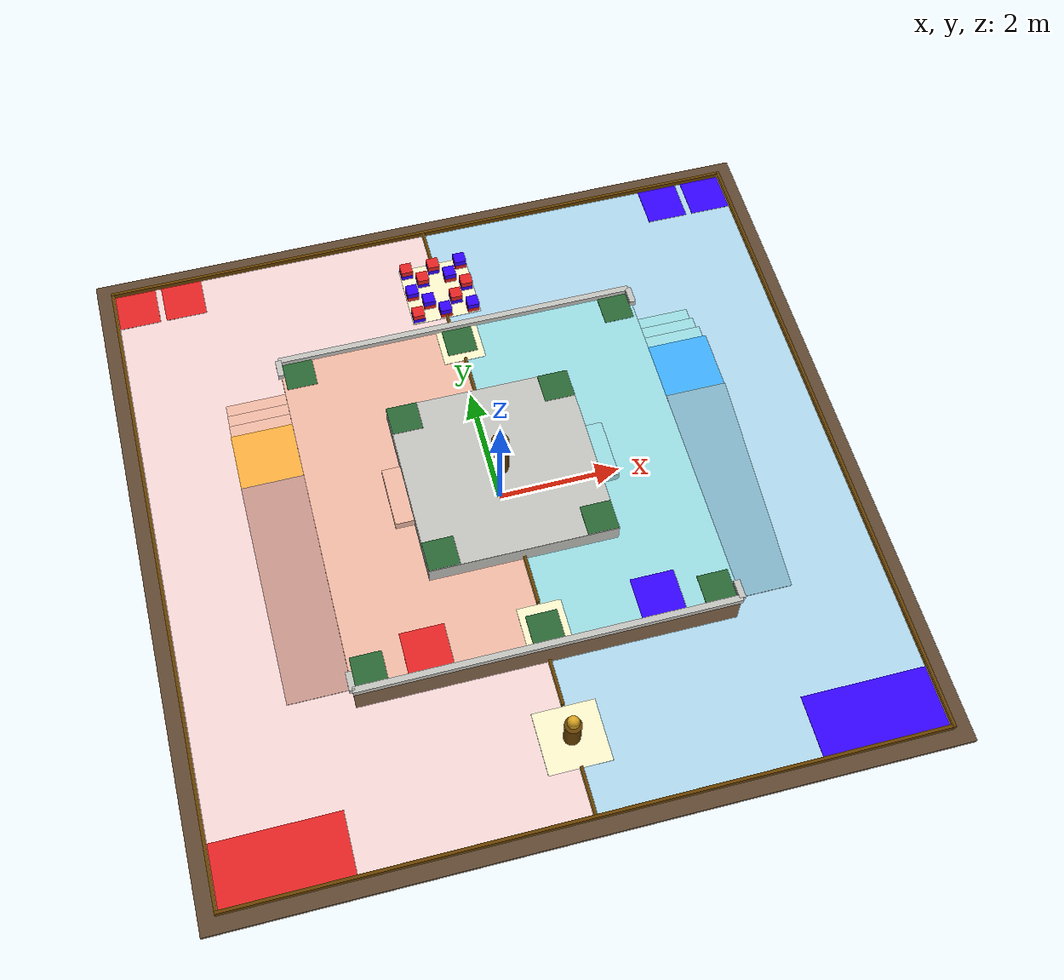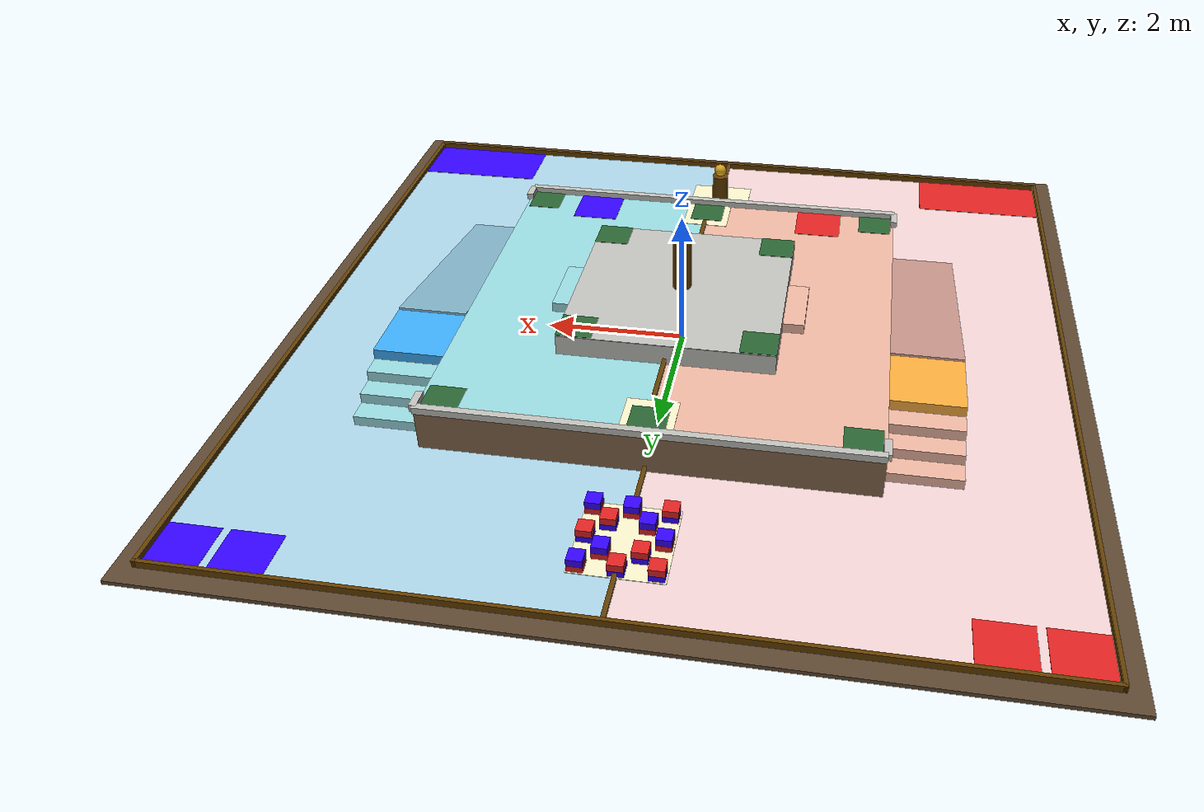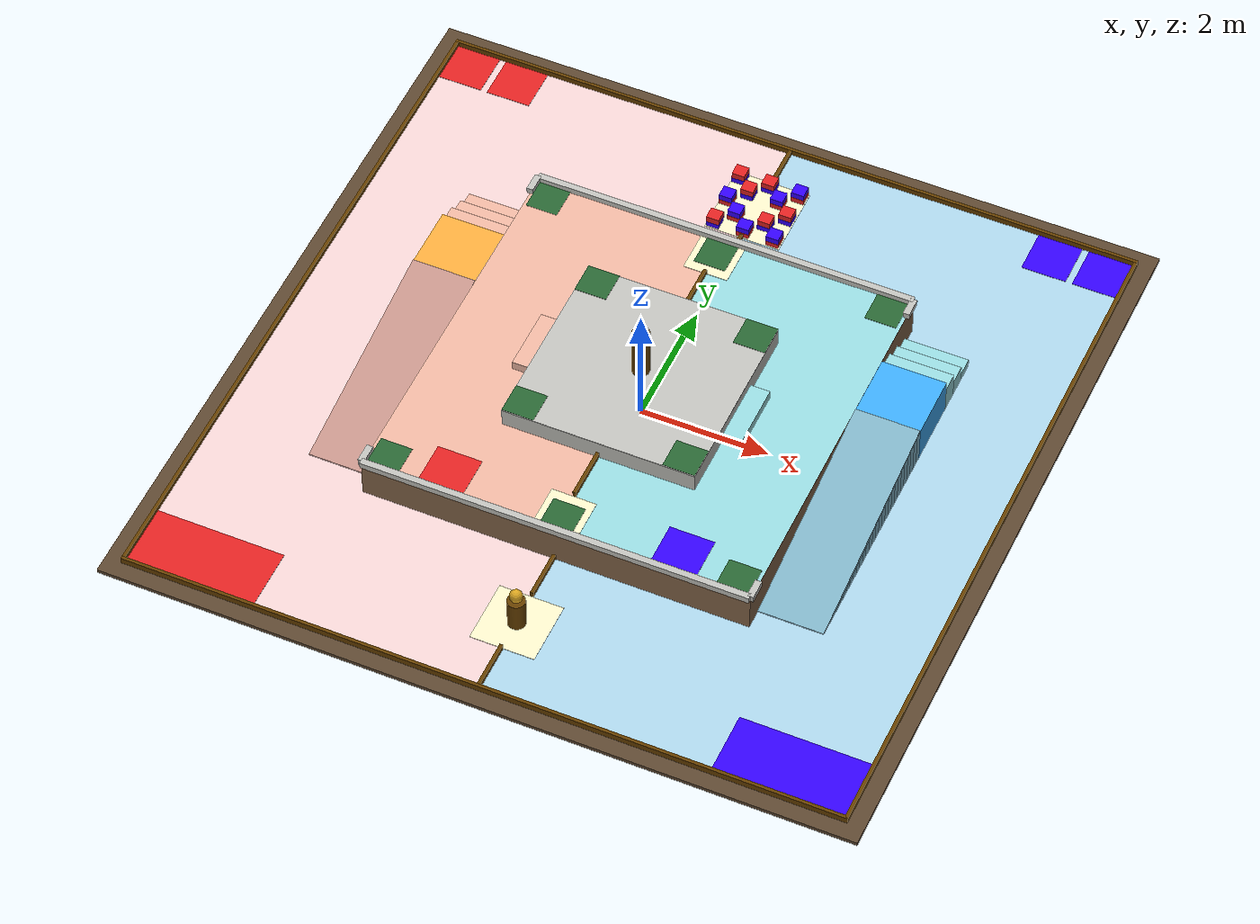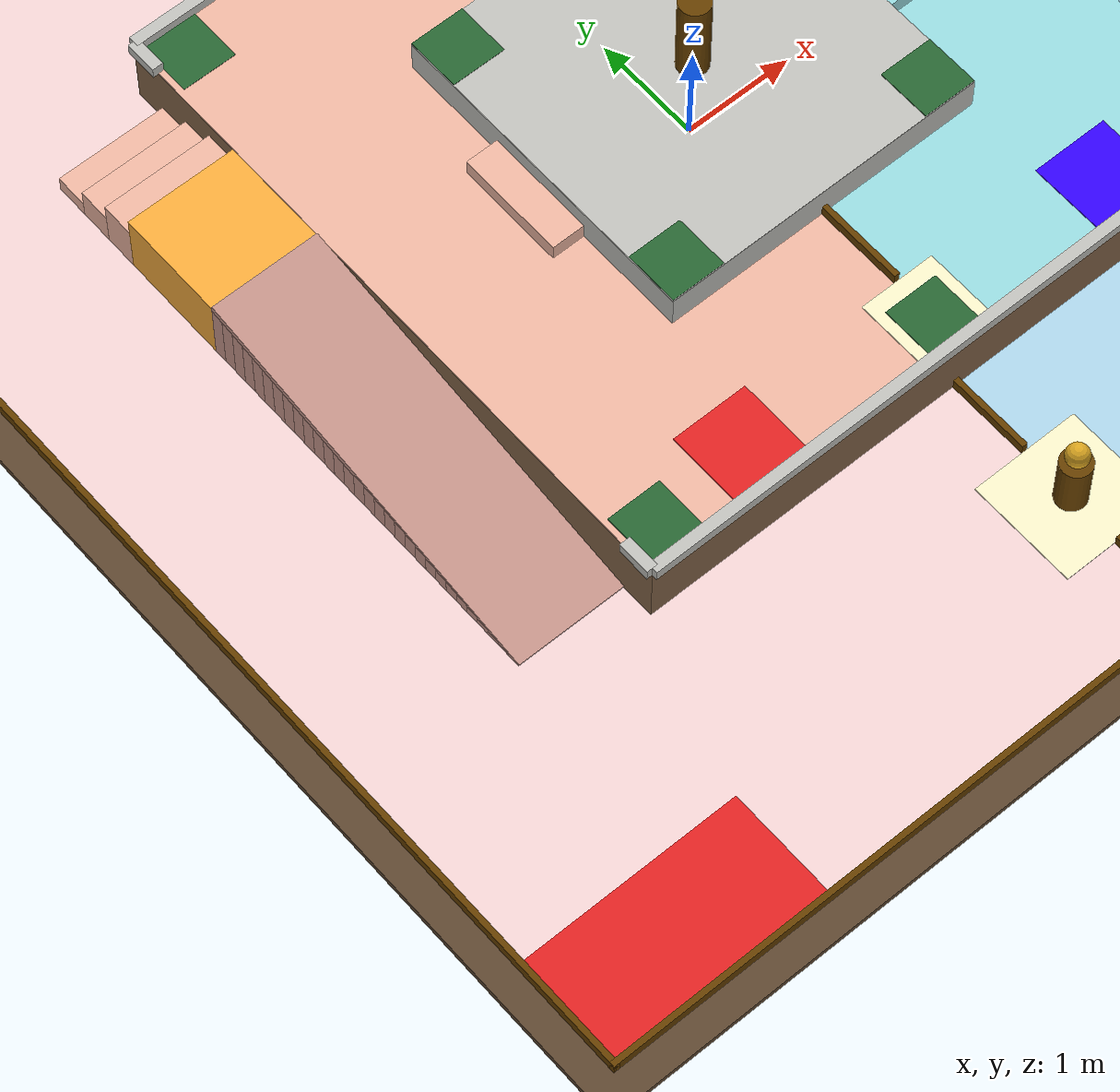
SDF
<sdf version="1.7">
 <world name="robocon2027_arena">
  <physics type="ode">
   <max_step_size>0.001</max_step_size>
   <real_time_update_rate>1000</real_time_update_rate>
   <real_time_factor>1</real_time_factor>
  </physics>
  <scene><ambient>0.55 0.55 0.62 1</ambient><background>0.24 0.26 0.3 1</background><shadows>1</shadows></scene>
  <light name="sun" type="directional">
   <pose>0 0 40 0 -0 0</pose>
   <diffuse>0.92 0.92 0.9 1</diffuse>
   <specular>0.3 0.3 0.3 1</specular>
   <direction>-0.55 -0.8 -1</direction>
   <attenuation><range>10</range></attenuation>
   <spot><inner_angle>0</inner_angle><outer_angle>0</outer_angle><falloff>0</falloff></spot>
  </light>
  <model name="field_base">
   <static>1</static>
   <pose>0 0 -0.03 0 -0 0</pose>
   <link name="link">
    <collision name="col"><geometry><box><size>11.6 11.6 0.06</size></box></geometry></collision>
    <visual name="vis">
     <geometry><box><size>11.6 11.6 0.06</size></box></geometry>
     <material>
      <ambient>0.361 0.275 0.188 1</ambient>
      <diffuse>0.361 0.275 0.188 1</diffuse>
      <specular>0.04 0.04 0.04 1</specular>
      <emissive>0 0 0 1</emissive>
     </material>
    </visual>
   </link>
  </model>
  <model name="catch_floor">
   <static>1</static>
   <pose>0 0 -0.25 0 -0 0</pose>
   <link name="link">
    <collision name="col">
     <geometry><plane><normal>0 0 1</normal><size>200 200</size></plane></geometry>
    </collision>
   </link>
  </model>
  <model name="l1_platform">
   <static>1</static>
   <pose>0 0 0.3 0 -0 0</pose>
   <link name="link">
    <collision name="col"><geometry><box><size>6 6 0.6</size></box></geometry></collision>
    <visual name="vis">
     <geometry><box><size>6 6 0.6</size></box></geometry>
     <material>
      <ambient>0.51 0.392 0.282 1</ambient>
      <diffuse>0.51 0.392 0.282 1</diffuse>
      <specular>0.04 0.04 0.04 1</specular>
      <emissive>0 0 0 1</emissive>
     </material>
    </visual>
   </link>
  </model>
  <model name="l2_platform">
   <static>1</static>
   <pose>0 0 0.75 0 -0 0</pose>
   <link name="link">
    <collision name="col"><geometry><box><size>3 3 0.3</size></box></geometry></collision>
    <visual name="vis">
     <geometry><box><size>3 3 0.3</size></box></geometry>
     <material>
      <ambient>0.745 0.745 0.725 1</ambient>
      <diffuse>0.745 0.745 0.725 1</diffuse>
      <specular>0.04 0.04 0.04 1</specular>
      <emissive>0 0 0 1</emissive>
     </material>
    </visual>
   </link>
  </model>
  <model name="mustika_pillar">
   <static>1</static>
   <pose>0 -4.25 0.25 0 -0 0</pose>
   <link name="link">
    <collision name="col">
     <geometry><cylinder><radius>0.135</radius><length>0.5</length></cylinder></geometry>
    </collision>
    <visual name="vis">
     <geometry><cylinder><radius>0.135</radius><length>0.5</length></cylinder></geometry>
     <material>
      <ambient>0.392 0.243 0 1</ambient>
      <diffuse>0.392 0.243 0 1</diffuse>
      <specular>0.04 0.04 0.04 1</specular>
      <emissive>0 0 0 1</emissive>
     </material>
    </visual>
   </link>
  </model>
  <model name="mustika_ball">
   <static>1</static>
   <pose>0 -4.25 0.6 0 -0 0</pose>
   <link name="link">
    <inertial>
     <mass>0.27</mass>
     <inertia><ixx>0.00108</ixx><iyy>0.00108</iyy><izz>0.00108</izz><ixy>0</ixy><ixz>0</ixz><iyz>0</iyz></inertia>
    </inertial>
    <collision name="col"><geometry><sphere><radius>0.1</radius></sphere></geometry></collision>
    <visual name="vis">
     <geometry><sphere><radius>0.1</radius></sphere></geometry>
     <material>
      <ambient>0.855 0.647 0.125 1</ambient>
      <diffuse>0.855 0.647 0.125 1</diffuse>
      <specular>0.04 0.04 0.04 1</specular>
      <emissive>0 0 0 1</emissive>
     </material>
    </visual>
   </link>
  </model>
  <model name="central_pillar">
   <static>1</static>
   <pose>0 0 1.3 0 -0 0</pose>
   <link name="link">
    <collision name="col">
     <geometry><cylinder><radius>0.135</radius><length>0.8</length></cylinder></geometry>
    </collision>
    <visual name="vis">
     <geometry><cylinder><radius>0.135</radius><length>0.8</length></cylinder></geometry>
     <material>
      <ambient>0.392 0.243 0 1</ambient>
      <diffuse>0.392 0.243 0 1</diffuse>
      <specular>0.04 0.04 0.04 1</specular>
      <emissive>0 0 0 1</emissive>
     </material>
    </visual>
   </link>
  </model>
  <model name="fence_pN">
   <static>1</static>
   <pose>0 5.525 0.05 0 -0 0</pose>
   <link name="link">
    <collision name="col"><geometry><box><size>11.1 0.05 0.1</size></box></geometry></collision>
    <visual name="vis">
     <geometry><box><size>11.1 0.05 0.1</size></box></geometry>
     <material>
      <ambient>0.392 0.243 0 1</ambient>
      <diffuse>0.392 0.243 0 1</diffuse>
      <specular>0.04 0.04 0.04 1</specular>
      <emissive>0 0 0 1</emissive>
     </material>
    </visual>
   </link>
  </model>
  <model name="fence_pS">
   <static>1</static>
   <pose>0 -5.525 0.05 0 -0 0</pose>
   <link name="link">
    <collision name="col"><geometry><box><size>11.1 0.05 0.1</size></box></geometry></collision>
    <visual name="vis">
     <geometry><box><size>11.1 0.05 0.1</size></box></geometry>
     <material>
      <ambient>0.392 0.243 0 1</ambient>
      <diffuse>0.392 0.243 0 1</diffuse>
      <specular>0.04 0.04 0.04 1</specular>
      <emissive>0 0 0 1</emissive>
     </material>
    </visual>
   </link>
  </model>
  <model name="fence_pE">
   <static>1</static>
   <pose>5.525 0 0.05 0 -0 0</pose>
   <link name="link">
    <collision name="col"><geometry><box><size>0.05 11.1 0.1</size></box></geometry></collision>
    <visual name="vis">
     <geometry><box><size>0.05 11.1 0.1</size></box></geometry>
     <material>
      <ambient>0.392 0.243 0 1</ambient>
      <diffuse>0.392 0.243 0 1</diffuse>
      <specular>0.04 0.04 0.04 1</specular>
      <emissive>0 0 0 1</emissive>
     </material>
    </visual>
   </link>
  </model>
  <model name="fence_pW">
   <static>1</static>
   <pose>-5.525 0 0.05 0 -0 0</pose>
   <link name="link">
    <collision name="col"><geometry><box><size>0.05 11.1 0.1</size></box></geometry></collision>
    <visual name="vis">
     <geometry><box><size>0.05 11.1 0.1</size></box></geometry>
     <material>
      <ambient>0.392 0.243 0 1</ambient>
      <diffuse>0.392 0.243 0 1</diffuse>
      <specular>0.04 0.04 0.04 1</specular>
      <emissive>0 0 0 1</emissive>
     </material>
    </visual>
   </link>
  </model>
  <model name="gdiv_0">
   <static>1</static>
   <pose>0 3.325 0.05 0 -0 0</pose>
   <link name="link">
    <collision name="col"><geometry><box><size>0.05 0.65 0.1</size></box></geometry></collision>
    <visual name="vis">
     <geometry><box><size>0.05 0.65 0.1</size></box></geometry>
     <material>
      <ambient>0.392 0.243 0 1</ambient>
      <diffuse>0.392 0.243 0 1</diffuse>
      <specular>0.04 0.04 0.04 1</specular>
      <emissive>0 0 0 1</emissive>
     </material>
    </visual>
   </link>
  </model>
  <model name="gdiv_1">
   <static>1</static>
   <pose>0 5.175 0.05 0 -0 0</pose>
   <link name="link">
    <collision name="col"><geometry><box><size>0.05 0.65 0.1</size></box></geometry></collision>
    <visual name="vis">
     <geometry><box><size>0.05 0.65 0.1</size></box></geometry>
     <material>
      <ambient>0.392 0.243 0 1</ambient>
      <diffuse>0.392 0.243 0 1</diffuse>
      <specular>0.04 0.04 0.04 1</specular>
      <emissive>0 0 0 1</emissive>
     </material>
    </visual>
   </link>
  </model>
  <model name="gdiv_2">
   <static>1</static>
   <pose>0 -3.375 0.05 0 -0 0</pose>
   <link name="link">
    <collision name="col"><geometry><box><size>0.05 0.75 0.1</size></box></geometry></collision>
    <visual name="vis">
     <geometry><box><size>0.05 0.75 0.1</size></box></geometry>
     <material>
      <ambient>0.392 0.243 0 1</ambient>
      <diffuse>0.392 0.243 0 1</diffuse>
      <specular>0.04 0.04 0.04 1</specular>
      <emissive>0 0 0 1</emissive>
     </material>
    </visual>
   </link>
  </model>
  <model name="gdiv_3">
   <static>1</static>
   <pose>0 -5.125 0.05 0 -0 0</pose>
   <link name="link">
    <collision name="col"><geometry><box><size>0.05 0.75 0.1</size></box></geometry></collision>
    <visual name="vis">
     <geometry><box><size>0.05 0.75 0.1</size></box></geometry>
     <material>
      <ambient>0.392 0.243 0 1</ambient>
      <diffuse>0.392 0.243 0 1</diffuse>
      <specular>0.04 0.04 0.04 1</specular>
      <emissive>0 0 0 1</emissive>
     </material>
    </visual>
   </link>
  </model>
  <model name="ddiv_0">
   <static>1</static>
   <pose>0 1.9 0.65 0 -0 0</pose>
   <link name="link">
    <collision name="col"><geometry><box><size>0.05 0.8 0.1</size></box></geometry></collision>
    <visual name="vis">
     <geometry><box><size>0.05 0.8 0.1</size></box></geometry>
     <material>
      <ambient>0.392 0.243 0 1</ambient>
      <diffuse>0.392 0.243 0 1</diffuse>
      <specular>0.04 0.04 0.04 1</specular>
      <emissive>0 0 0 1</emissive>
     </material>
    </visual>
   </link>
  </model>
  <model name="ddiv_1">
   <static>1</static>
   <pose>0 -1.9 0.65 0 -0 0</pose>
   <link name="link">
    <collision name="col"><geometry><box><size>0.05 0.8 0.1</size></box></geometry></collision>
    <visual name="vis">
     <geometry><box><size>0.05 0.8 0.1</size></box></geometry>
     <material>
      <ambient>0.392 0.243 0 1</ambient>
      <diffuse>0.392 0.243 0 1</diffuse>
      <specular>0.04 0.04 0.04 1</specular>
      <emissive>0 0 0 1</emissive>
     </material>
    </visual>
   </link>
  </model>
  <model name="ramp_red">
   <static>1</static>
   <pose>-3.5 -0.95 0.3 0 -0.169778 1.5708</pose>
   <link name="link">
    <collision name="col"><geometry><box><size>3.55 1 0.06</size></box></geometry></collision>
    <visual name="vis">
     <geometry><box><size>3.55 1 0.06</size></box></geometry>
     <material>
      <ambient>0.784 0.588 0.549 1</ambient>
      <diffuse>0.784 0.588 0.549 1</diffuse>
      <specular>0.04 0.04 0.04 1</specular>
      <emissive>0 0 0 1</emissive>
     </material>
    </visual>
   </link>
  </model>
  <model name="rampsup_red_1">
   <static>1</static>
   <pose>-3.5 -2.525 0.015 0 -0 0</pose>
   <link name="link">
    <collision name="col"><geometry><box><size>1 0.118667 0.03</size></box></geometry></collision>
    <visual name="vis">
     <geometry><box><size>1 0.118667 0.03</size></box></geometry>
     <material>
      <ambient>0.784 0.588 0.549 1</ambient>
      <diffuse>0.784 0.588 0.549 1</diffuse>
      <specular>0.04 0.04 0.04 1</specular>
      <emissive>0 0 0 1</emissive>
     </material>
    </visual>
   </link>
  </model>
  <model name="rampsup_red_2">
   <static>1</static>
   <pose>-3.5 -2.4083 0.025 0 -0 0</pose>
   <link name="link">
    <collision name="col"><geometry><box><size>1 0.118667 0.05</size></box></geometry></collision>
    <visual name="vis">
     <geometry><box><size>1 0.118667 0.05</size></box></geometry>
     <material>
      <ambient>0.784 0.588 0.549 1</ambient>
      <diffuse>0.784 0.588 0.549 1</diffuse>
      <specular>0.04 0.04 0.04 1</specular>
      <emissive>0 0 0 1</emissive>
     </material>
    </visual>
   </link>
  </model>
  <model name="rampsup_red_3">
   <static>1</static>
   <pose>-3.5 -2.2917 0.035 0 -0 0</pose>
   <link name="link">
    <collision name="col"><geometry><box><size>1 0.118667 0.07</size></box></geometry></collision>
    <visual name="vis">
     <geometry><box><size>1 0.118667 0.07</size></box></geometry>
     <material>
      <ambient>0.784 0.588 0.549 1</ambient>
      <diffuse>0.784 0.588 0.549 1</diffuse>
      <specular>0.04 0.04 0.04 1</specular>
      <emissive>0 0 0 1</emissive>
     </material>
    </visual>
   </link>
  </model>
  <model name="rampsup_red_4">
   <static>1</static>
   <pose>-3.5 -2.175 0.045 0 -0 0</pose>
   <link name="link">
    <collision name="col"><geometry><box><size>1 0.118667 0.09</size></box></geometry></collision>
    <visual name="vis">
     <geometry><box><size>1 0.118667 0.09</size></box></geometry>
     <material>
      <ambient>0.784 0.588 0.549 1</ambient>
      <diffuse>0.784 0.588 0.549 1</diffuse>
      <specular>0.04 0.04 0.04 1</specular>
      <emissive>0 0 0 1</emissive>
     </material>
    </visual>
   </link>
  </model>
  <model name="rampsup_red_5">
   <static>1</static>
   <pose>-3.5 -2.0583 0.055 0 -0 0</pose>
   <link name="link">
    <collision name="col"><geometry><box><size>1 0.118667 0.11</size></box></geometry></collision>
    <visual name="vis">
     <geometry><box><size>1 0.118667 0.11</size></box></geometry>
     <material>
      <ambient>0.784 0.588 0.549 1</ambient>
      <diffuse>0.784 0.588 0.549 1</diffuse>
      <specular>0.04 0.04 0.04 1</specular>
      <emissive>0 0 0 1</emissive>
     </material>
    </visual>
   </link>
  </model>
  <model name="rampsup_red_6">
   <static>1</static>
   <pose>-3.5 -1.9417 0.065 0 -0 0</pose>
   <link name="link">
    <collision name="col"><geometry><box><size>1 0.118667 0.13</size></box></geometry></collision>
    <visual name="vis">
     <geometry><box><size>1 0.118667 0.13</size></box></geometry>
     <material>
      <ambient>0.784 0.588 0.549 1</ambient>
      <diffuse>0.784 0.588 0.549 1</diffuse>
      <specular>0.04 0.04 0.04 1</specular>
      <emissive>0 0 0 1</emissive>
     </material>
    </visual>
   </link>
  </model>
  <model name="rampsup_red_7">
   <static>1</static>
   <pose>-3.5 -1.825 0.075 0 -0 0</pose>
   <link name="link">
    <collision name="col"><geometry><box><size>1 0.118667 0.15</size></box></geometry></collision>
    <visual name="vis">
     <geometry><box><size>1 0.118667 0.15</size></box></geometry>
     <material>
      <ambient>0.784 0.588 0.549 1</ambient>
      <diffuse>0.784 0.588 0.549 1</diffuse>
      <specular>0.04 0.04 0.04 1</specular>
      <emissive>0 0 0 1</emissive>
     </material>
    </visual>
   </link>
  </model>
  <model name="rampsup_red_8">
   <static>1</static>
   <pose>-3.5 -1.7083 0.085 0 -0 0</pose>
   <link name="link">
    <collision name="col"><geometry><box><size>1 0.118667 0.17</size></box></geometry></collision>
    <visual name="vis">
     <geometry><box><size>1 0.118667 0.17</size></box></geometry>
     <material>
      <ambient>0.784 0.588 0.549 1</ambient>
      <diffuse>0.784 0.588 0.549 1</diffuse>
      <specular>0.04 0.04 0.04 1</specular>
      <emissive>0 0 0 1</emissive>
     </material>
    </visual>
   </link>
  </model>
  <model name="rampsup_red_9">
   <static>1</static>
   <pose>-3.5 -1.5917 0.095 0 -0 0</pose>
   <link name="link">
    <collision name="col"><geometry><box><size>1 0.118667 0.19</size></box></geometry></collision>
    <visual name="vis">
     <geometry><box><size>1 0.118667 0.19</size></box></geometry>
     <material>
      <ambient>0.784 0.588 0.549 1</ambient>
      <diffuse>0.784 0.588 0.549 1</diffuse>
      <specular>0.04 0.04 0.04 1</specular>
      <emissive>0 0 0 1</emissive>
     </material>
    </visual>
   </link>
  </model>
  <model name="rampsup_red_10">
   <static>1</static>
   <pose>-3.5 -1.475 0.105 0 -0 0</pose>
   <link name="link">
    <collision name="col"><geometry><box><size>1 0.118667 0.21</size></box></geometry></collision>
    <visual name="vis">
     <geometry><box><size>1 0.118667 0.21</size></box></geometry>
     <material>
      <ambient>0.784 0.588 0.549 1</ambient>
      <diffuse>0.784 0.588 0.549 1</diffuse>
      <specular>0.04 0.04 0.04 1</specular>
      <emissive>0 0 0 1</emissive>
     </material>
    </visual>
   </link>
  </model>
  <model name="rampsup_red_11">
   <static>1</static>
   <pose>-3.5 -1.3583 0.115 0 -0 0</pose>
   <link name="link">
    <collision name="col"><geometry><box><size>1 0.118667 0.23</size></box></geometry></collision>
    <visual name="vis">
     <geometry><box><size>1 0.118667 0.23</size></box></geometry>
     <material>
      <ambient>0.784 0.588 0.549 1</ambient>
      <diffuse>0.784 0.588 0.549 1</diffuse>
      <specular>0.04 0.04 0.04 1</specular>
      <emissive>0 0 0 1</emissive>
     </material>
    </visual>
   </link>
  </model>
  <model name="rampsup_red_12">
   <static>1</static>
   <pose>-3.5 -1.2417 0.125 0 -0 0</pose>
   <link name="link">
    <collision name="col"><geometry><box><size>1 0.118667 0.25</size></box></geometry></collision>
    <visual name="vis">
     <geometry><box><size>1 0.118667 0.25</size></box></geometry>
     <material>
      <ambient>0.784 0.588 0.549 1</ambient>
      <diffuse>0.784 0.588 0.549 1</diffuse>
      <specular>0.04 0.04 0.04 1</specular>
      <emissive>0 0 0 1</emissive>
     </material>
    </visual>
   </link>
  </model>
  <model name="rampsup_red_13">
   <static>1</static>
   <pose>-3.5 -1.125 0.135 0 -0 0</pose>
   <link name="link">
    <collision name="col"><geometry><box><size>1 0.118667 0.27</size></box></geometry></collision>
    <visual name="vis">
     <geometry><box><size>1 0.118667 0.27</size></box></geometry>
     <material>
      <ambient>0.784 0.588 0.549 1</ambient>
      <diffuse>0.784 0.588 0.549 1</diffuse>
      <specular>0.04 0.04 0.04 1</specular>
      <emissive>0 0 0 1</emissive>
     </material>
    </visual>
   </link>
  </model>
  <model name="rampsup_red_14">
   <static>1</static>
   <pose>-3.5 -1.0083 0.145 0 -0 0</pose>
   <link name="link">
    <collision name="col"><geometry><box><size>1 0.118667 0.29</size></box></geometry></collision>
    <visual name="vis">
     <geometry><box><size>1 0.118667 0.29</size></box></geometry>
     <material>
      <ambient>0.784 0.588 0.549 1</ambient>
      <diffuse>0.784 0.588 0.549 1</diffuse>
      <specular>0.04 0.04 0.04 1</specular>
      <emissive>0 0 0 1</emissive>
     </material>
    </visual>
   </link>
  </model>
  <model name="rampsup_red_15">
   <static>1</static>
   <pose>-3.5 -0.8917 0.155 0 -0 0</pose>
   <link name="link">
    <collision name="col"><geometry><box><size>1 0.118667 0.31</size></box></geometry></collision>
    <visual name="vis">
     <geometry><box><size>1 0.118667 0.31</size></box></geometry>
     <material>
      <ambient>0.784 0.588 0.549 1</ambient>
      <diffuse>0.784 0.588 0.549 1</diffuse>
      <specular>0.04 0.04 0.04 1</specular>
      <emissive>0 0 0 1</emissive>
     </material>
    </visual>
   </link>
  </model>
  <model name="rampsup_red_16">
   <static>1</static>
   <pose>-3.5 -0.775 0.165 0 -0 0</pose>
   <link name="link">
    <collision name="col"><geometry><box><size>1 0.118667 0.33</size></box></geometry></collision>
    <visual name="vis">
     <geometry><box><size>1 0.118667 0.33</size></box></geometry>
     <material>
      <ambient>0.784 0.588 0.549 1</ambient>
      <diffuse>0.784 0.588 0.549 1</diffuse>
      <specular>0.04 0.04 0.04 1</specular>
      <emissive>0 0 0 1</emissive>
     </material>
    </visual>
   </link>
  </model>
  <model name="rampsup_red_17">
   <static>1</static>
   <pose>-3.5 -0.6583 0.175 0 -0 0</pose>
   <link name="link">
    <collision name="col"><geometry><box><size>1 0.118667 0.35</size></box></geometry></collision>
    <visual name="vis">
     <geometry><box><size>1 0.118667 0.35</size></box></geometry>
     <material>
      <ambient>0.784 0.588 0.549 1</ambient>
      <diffuse>0.784 0.588 0.549 1</diffuse>
      <specular>0.04 0.04 0.04 1</specular>
      <emissive>0 0 0 1</emissive>
     </material>
    </visual>
   </link>
  </model>
  <model name="rampsup_red_18">
   <static>1</static>
   <pose>-3.5 -0.5417 0.185 0 -0 0</pose>
   <link name="link">
    <collision name="col"><geometry><box><size>1 0.118667 0.37</size></box></geometry></collision>
    <visual name="vis">
     <geometry><box><size>1 0.118667 0.37</size></box></geometry>
     <material>
      <ambient>0.784 0.588 0.549 1</ambient>
      <diffuse>0.784 0.588 0.549 1</diffuse>
      <specular>0.04 0.04 0.04 1</specular>
      <emissive>0 0 0 1</emissive>
     </material>
    </visual>
   </link>
  </model>
  <model name="rampsup_red_19">
   <static>1</static>
   <pose>-3.5 -0.425 0.195 0 -0 0</pose>
   <link name="link">
    <collision name="col"><geometry><box><size>1 0.118667 0.39</size></box></geometry></collision>
    <visual name="vis">
     <geometry><box><size>1 0.118667 0.39</size></box></geometry>
     <material>
      <ambient>0.784 0.588 0.549 1</ambient>
      <diffuse>0.784 0.588 0.549 1</diffuse>
      <specular>0.04 0.04 0.04 1</specular>
      <emissive>0 0 0 1</emissive>
     </material>
    </visual>
   </link>
  </model>
  <model name="rampsup_red_20">
   <static>1</static>
   <pose>-3.5 -0.3083 0.205 0 -0 0</pose>
   <link name="link">
    <collision name="col"><geometry><box><size>1 0.118667 0.41</size></box></geometry></collision>
    <visual name="vis">
     <geometry><box><size>1 0.118667 0.41</size></box></geometry>
     <material>
      <ambient>0.784 0.588 0.549 1</ambient>
      <diffuse>0.784 0.588 0.549 1</diffuse>
      <specular>0.04 0.04 0.04 1</specular>
      <emissive>0 0 0 1</emissive>
     </material>
    </visual>
   </link>
  </model>
  <model name="rampsup_red_21">
   <static>1</static>
   <pose>-3.5 -0.1917 0.215 0 -0 0</pose>
   <link name="link">
    <collision name="col"><geometry><box><size>1 0.118667 0.43</size></box></geometry></collision>
    <visual name="vis">
     <geometry><box><size>1 0.118667 0.43</size></box></geometry>
     <material>
      <ambient>0.784 0.588 0.549 1</ambient>
      <diffuse>0.784 0.588 0.549 1</diffuse>
      <specular>0.04 0.04 0.04 1</specular>
      <emissive>0 0 0 1</emissive>
     </material>
    </visual>
   </link>
  </model>
  <model name="rampsup_red_22">
   <static>1</static>
   <pose>-3.5 -0.075 0.225 0 -0 0</pose>
   <link name="link">
    <collision name="col"><geometry><box><size>1 0.118667 0.45</size></box></geometry></collision>
    <visual name="vis">
     <geometry><box><size>1 0.118667 0.45</size></box></geometry>
     <material>
      <ambient>0.784 0.588 0.549 1</ambient>
      <diffuse>0.784 0.588 0.549 1</diffuse>
      <specular>0.04 0.04 0.04 1</specular>
      <emissive>0 0 0 1</emissive>
     </material>
    </visual>
   </link>
  </model>
  <model name="rampsup_red_23">
   <static>1</static>
   <pose>-3.5 0.0417 0.235 0 -0 0</pose>
   <link name="link">
    <collision name="col"><geometry><box><size>1 0.118667 0.47</size></box></geometry></collision>
    <visual name="vis">
     <geometry><box><size>1 0.118667 0.47</size></box></geometry>
     <material>
      <ambient>0.784 0.588 0.549 1</ambient>
      <diffuse>0.784 0.588 0.549 1</diffuse>
      <specular>0.04 0.04 0.04 1</specular>
      <emissive>0 0 0 1</emissive>
     </material>
    </visual>
   </link>
  </model>
  <model name="rampsup_red_24">
   <static>1</static>
   <pose>-3.5 0.1583 0.245 0 -0 0</pose>
   <link name="link">
    <collision name="col"><geometry><box><size>1 0.118667 0.49</size></box></geometry></collision>
    <visual name="vis">
     <geometry><box><size>1 0.118667 0.49</size></box></geometry>
     <material>
      <ambient>0.784 0.588 0.549 1</ambient>
      <diffuse>0.784 0.588 0.549 1</diffuse>
      <specular>0.04 0.04 0.04 1</specular>
      <emissive>0 0 0 1</emissive>
     </material>
    </visual>
   </link>
  </model>
  <model name="rampsup_red_25">
   <static>1</static>
   <pose>-3.5 0.275 0.255 0 -0 0</pose>
   <link name="link">
    <collision name="col"><geometry><box><size>1 0.118667 0.51</size></box></geometry></collision>
    <visual name="vis">
     <geometry><box><size>1 0.118667 0.51</size></box></geometry>
     <material>
      <ambient>0.784 0.588 0.549 1</ambient>
      <diffuse>0.784 0.588 0.549 1</diffuse>
      <specular>0.04 0.04 0.04 1</specular>
      <emissive>0 0 0 1</emissive>
     </material>
    </visual>
   </link>
  </model>
  <model name="rampsup_red_26">
   <static>1</static>
   <pose>-3.5 0.3917 0.265 0 -0 0</pose>
   <link name="link">
    <collision name="col"><geometry><box><size>1 0.118667 0.53</size></box></geometry></collision>
    <visual name="vis">
     <geometry><box><size>1 0.118667 0.53</size></box></geometry>
     <material>
      <ambient>0.784 0.588 0.549 1</ambient>
      <diffuse>0.784 0.588 0.549 1</diffuse>
      <specular>0.04 0.04 0.04 1</specular>
      <emissive>0 0 0 1</emissive>
     </material>
    </visual>
   </link>
  </model>
  <model name="rampsup_red_27">
   <static>1</static>
   <pose>-3.5 0.5083 0.275 0 -0 0</pose>
   <link name="link">
    <collision name="col"><geometry><box><size>1 0.118667 0.55</size></box></geometry></collision>
    <visual name="vis">
     <geometry><box><size>1 0.118667 0.55</size></box></geometry>
     <material>
      <ambient>0.784 0.588 0.549 1</ambient>
      <diffuse>0.784 0.588 0.549 1</diffuse>
      <specular>0.04 0.04 0.04 1</specular>
      <emissive>0 0 0 1</emissive>
     </material>
    </visual>
   </link>
  </model>
  <model name="rampsup_red_28">
   <static>1</static>
   <pose>-3.5 0.625 0.285 0 -0 0</pose>
   <link name="link">
    <collision name="col"><geometry><box><size>1 0.118667 0.57</size></box></geometry></collision>
    <visual name="vis">
     <geometry><box><size>1 0.118667 0.57</size></box></geometry>
     <material>
      <ambient>0.784 0.588 0.549 1</ambient>
      <diffuse>0.784 0.588 0.549 1</diffuse>
      <specular>0.04 0.04 0.04 1</specular>
      <emissive>0 0 0 1</emissive>
     </material>
    </visual>
   </link>
  </model>
  <model name="rampsup_red_29">
   <static>1</static>
   <pose>-3.5 0.7417 0.295 0 -0 0</pose>
   <link name="link">
    <collision name="col"><geometry><box><size>1 0.118667 0.59</size></box></geometry></collision>
    <visual name="vis">
     <geometry><box><size>1 0.118667 0.59</size></box></geometry>
     <material>
      <ambient>0.784 0.588 0.549 1</ambient>
      <diffuse>0.784 0.588 0.549 1</diffuse>
      <specular>0.04 0.04 0.04 1</specular>
      <emissive>0 0 0 1</emissive>
     </material>
    </visual>
   </link>
  </model>
  <model name="plat_red">
   <static>1</static>
   <pose>-3.5 1.3 0.3 0 -0 0</pose>
   <link name="link">
    <collision name="col"><geometry><box><size>1 1 0.6</size></box></geometry></collision>
    <visual name="vis">
     <geometry><box><size>1 1 0.6</size></box></geometry>
     <material>
      <ambient>0.961 0.667 0.235 1</ambient>
      <diffuse>0.961 0.667 0.235 1</diffuse>
      <specular>0.04 0.04 0.04 1</specular>
      <emissive>0 0 0 1</emissive>
     </material>
    </visual>
   </link>
  </model>
  <model name="stp_red_0">
   <static>1</static>
   <pose>-3.5 1.95 0.225 0 -0 0</pose>
   <link name="link">
    <collision name="col"><geometry><box><size>1 0.3 0.45</size></box></geometry></collision>
    <visual name="vis">
     <geometry><box><size>1 0.3 0.45</size></box></geometry>
     <material>
      <ambient>0.922 0.706 0.627 1</ambient>
      <diffuse>0.922 0.706 0.627 1</diffuse>
      <specular>0.04 0.04 0.04 1</specular>
      <emissive>0 0 0 1</emissive>
     </material>
    </visual>
   </link>
  </model>
  <model name="stp_red_1">
   <static>1</static>
   <pose>-3.5 2.25 0.15 0 -0 0</pose>
   <link name="link">
    <collision name="col"><geometry><box><size>1 0.3 0.3</size></box></geometry></collision>
    <visual name="vis">
     <geometry><box><size>1 0.3 0.3</size></box></geometry>
     <material>
      <ambient>0.922 0.706 0.627 1</ambient>
      <diffuse>0.922 0.706 0.627 1</diffuse>
      <specular>0.04 0.04 0.04 1</specular>
      <emissive>0 0 0 1</emissive>
     </material>
    </visual>
   </link>
  </model>
  <model name="stp_red_2">
   <static>1</static>
   <pose>-3.5 2.55 0.075 0 -0 0</pose>
   <link name="link">
    <collision name="col"><geometry><box><size>1 0.3 0.15</size></box></geometry></collision>
    <visual name="vis">
     <geometry><box><size>1 0.3 0.15</size></box></geometry>
     <material>
      <ambient>0.922 0.706 0.627 1</ambient>
      <diffuse>0.922 0.706 0.627 1</diffuse>
      <specular>0.04 0.04 0.04 1</specular>
      <emissive>0 0 0 1</emissive>
     </material>
    </visual>
   </link>
  </model>
  <model name="st2_red">
   <static>1</static>
   <pose>-1.65 0 0.675 0 -0 0</pose>
   <link name="link">
    <collision name="col"><geometry><box><size>0.3 1 0.15</size></box></geometry></collision>
    <visual name="vis">
     <geometry><box><size>0.3 1 0.15</size></box></geometry>
     <material>
      <ambient>0.922 0.706 0.627 1</ambient>
      <diffuse>0.922 0.706 0.627 1</diffuse>
      <specular>0.04 0.04 0.04 1</specular>
      <emissive>0 0 0 1</emissive>
     </material>
    </visual>
   </link>
  </model>
  <model name="ramp_blue">
   <static>1</static>
   <pose>3.5 -0.95 0.3 0 -0.169778 1.5708</pose>
   <link name="link">
    <collision name="col"><geometry><box><size>3.55 1 0.06</size></box></geometry></collision>
    <visual name="vis">
     <geometry><box><size>3.55 1 0.06</size></box></geometry>
     <material>
      <ambient>0.51 0.706 0.784 1</ambient>
      <diffuse>0.51 0.706 0.784 1</diffuse>
      <specular>0.04 0.04 0.04 1</specular>
      <emissive>0 0 0 1</emissive>
     </material>
    </visual>
   </link>
  </model>
  <model name="rampsup_blue_1">
   <static>1</static>
   <pose>3.5 -2.525 0.015 0 -0 0</pose>
   <link name="link">
    <collision name="col"><geometry><box><size>1 0.118667 0.03</size></box></geometry></collision>
    <visual name="vis">
     <geometry><box><size>1 0.118667 0.03</size></box></geometry>
     <material>
      <ambient>0.51 0.706 0.784 1</ambient>
      <diffuse>0.51 0.706 0.784 1</diffuse>
      <specular>0.04 0.04 0.04 1</specular>
      <emissive>0 0 0 1</emissive>
     </material>
    </visual>
   </link>
  </model>
  <model name="rampsup_blue_2">
   <static>1</static>
   <pose>3.5 -2.4083 0.025 0 -0 0</pose>
   <link name="link">
    <collision name="col"><geometry><box><size>1 0.118667 0.05</size></box></geometry></collision>
    <visual name="vis">
     <geometry><box><size>1 0.118667 0.05</size></box></geometry>
     <material>
      <ambient>0.51 0.706 0.784 1</ambient>
      <diffuse>0.51 0.706 0.784 1</diffuse>
      <specular>0.04 0.04 0.04 1</specular>
      <emissive>0 0 0 1</emissive>
     </material>
    </visual>
   </link>
  </model>
  <model name="rampsup_blue_3">
   <static>1</static>
   <pose>3.5 -2.2917 0.035 0 -0 0</pose>
   <link name="link">
    <collision name="col"><geometry><box><size>1 0.118667 0.07</size></box></geometry></collision>
    <visual name="vis">
     <geometry><box><size>1 0.118667 0.07</size></box></geometry>
     <material>
      <ambient>0.51 0.706 0.784 1</ambient>
      <diffuse>0.51 0.706 0.784 1</diffuse>
      <specular>0.04 0.04 0.04 1</specular>
      <emissive>0 0 0 1</emissive>
     </material>
    </visual>
   </link>
  </model>
  <model name="rampsup_blue_4">
   <static>1</static>
   <pose>3.5 -2.175 0.045 0 -0 0</pose>
   <link name="link">
    <collision name="col"><geometry><box><size>1 0.118667 0.09</size></box></geometry></collision>
    <visual name="vis">
     <geometry><box><size>1 0.118667 0.09</size></box></geometry>
     <material>
      <ambient>0.51 0.706 0.784 1</ambient>
      <diffuse>0.51 0.706 0.784 1</diffuse>
      <specular>0.04 0.04 0.04 1</specular>
      <emissive>0 0 0 1</emissive>
     </material>
    </visual>
   </link>
  </model>
  <model name="rampsup_blue_5">
   <static>1</static>
   <pose>3.5 -2.0583 0.055 0 -0 0</pose>
   <link name="link">
    <collision name="col"><geometry><box><size>1 0.118667 0.11</size></box></geometry></collision>
    <visual name="vis">
     <geometry><box><size>1 0.118667 0.11</size></box></geometry>
     <material>
      <ambient>0.51 0.706 0.784 1</ambient>
      <diffuse>0.51 0.706 0.784 1</diffuse>
      <specular>0.04 0.04 0.04 1</specular>
      <emissive>0 0 0 1</emissive>
     </material>
    </visual>
   </link>
  </model>
  <model name="rampsup_blue_6">
   <static>1</static>
   <pose>3.5 -1.9417 0.065 0 -0 0</pose>
   <link name="link">
    <collision name="col"><geometry><box><size>1 0.118667 0.13</size></box></geometry></collision>
    <visual name="vis">
     <geometry><box><size>1 0.118667 0.13</size></box></geometry>
     <material>
      <ambient>0.51 0.706 0.784 1</ambient>
      <diffuse>0.51 0.706 0.784 1</diffuse>
      <specular>0.04 0.04 0.04 1</specular>
      <emissive>0 0 0 1</emissive>
     </material>
    </visual>
   </link>
  </model>
  <model name="rampsup_blue_7">
   <static>1</static>
   <pose>3.5 -1.825 0.075 0 -0 0</pose>
   <link name="link">
    <collision name="col"><geometry><box><size>1 0.118667 0.15</size></box></geometry></collision>
    <visual name="vis">
     <geometry><box><size>1 0.118667 0.15</size></box></geometry>
     <material>
      <ambient>0.51 0.706 0.784 1</ambient>
      <diffuse>0.51 0.706 0.784 1</diffuse>
      <specular>0.04 0.04 0.04 1</specular>
      <emissive>0 0 0 1</emissive>
     </material>
    </visual>
   </link>
  </model>
  <model name="rampsup_blue_8">
   <static>1</static>
   <pose>3.5 -1.7083 0.085 0 -0 0</pose>
   <link name="link">
    <collision name="col"><geometry><box><size>1 0.118667 0.17</size></box></geometry></collision>
    <visual name="vis">
     <geometry><box><size>1 0.118667 0.17</size></box></geometry>
     <material>
      <ambient>0.51 0.706 0.784 1</ambient>
      <diffuse>0.51 0.706 0.784 1</diffuse>
      <specular>0.04 0.04 0.04 1</specular>
      <emissive>0 0 0 1</emissive>
     </material>
    </visual>
   </link>
  </model>
  <model name="rampsup_blue_9">
   <static>1</static>
   <pose>3.5 -1.5917 0.095 0 -0 0</pose>
   <link name="link">
    <collision name="col"><geometry><box><size>1 0.118667 0.19</size></box></geometry></collision>
    <visual name="vis">
     <geometry><box><size>1 0.118667 0.19</size></box></geometry>
     <material>
      <ambient>0.51 0.706 0.784 1</ambient>
      <diffuse>0.51 0.706 0.784 1</diffuse>
      <specular>0.04 0.04 0.04 1</specular>
      <emissive>0 0 0 1</emissive>
     </material>
    </visual>
   </link>
  </model>
  <model name="rampsup_blue_10">
   <static>1</static>
   <pose>3.5 -1.475 0.105 0 -0 0</pose>
   <link name="link">
    <collision name="col"><geometry><box><size>1 0.118667 0.21</size></box></geometry></collision>
    <visual name="vis">
     <geometry><box><size>1 0.118667 0.21</size></box></geometry>
     <material>
      <ambient>0.51 0.706 0.784 1</ambient>
      <diffuse>0.51 0.706 0.784 1</diffuse>
      <specular>0.04 0.04 0.04 1</specular>
      <emissive>0 0 0 1</emissive>
     </material>
    </visual>
   </link>
  </model>
  <model name="rampsup_blue_11">
   <static>1</static>
   <pose>3.5 -1.3583 0.115 0 -0 0</pose>
   <link name="link">
    <collision name="col"><geometry><box><size>1 0.118667 0.23</size></box></geometry></collision>
    <visual name="vis">
     <geometry><box><size>1 0.118667 0.23</size></box></geometry>
     <material>
      <ambient>0.51 0.706 0.784 1</ambient>
      <diffuse>0.51 0.706 0.784 1</diffuse>
      <specular>0.04 0.04 0.04 1</specular>
      <emissive>0 0 0 1</emissive>
     </material>
    </visual>
   </link>
  </model>
  <model name="rampsup_blue_12">
   <static>1</static>
   <pose>3.5 -1.2417 0.125 0 -0 0</pose>
   <link name="link">
    <collision name="col"><geometry><box><size>1 0.118667 0.25</size></box></geometry></collision>
    <visual name="vis">
     <geometry><box><size>1 0.118667 0.25</size></box></geometry>
     <material>
      <ambient>0.51 0.706 0.784 1</ambient>
      <diffuse>0.51 0.706 0.784 1</diffuse>
      <specular>0.04 0.04 0.04 1</specular>
      <emissive>0 0 0 1</emissive>
     </material>
    </visual>
   </link>
  </model>
  <model name="rampsup_blue_13">
   <static>1</static>
   <pose>3.5 -1.125 0.135 0 -0 0</pose>
   <link name="link">
    <collision name="col"><geometry><box><size>1 0.118667 0.27</size></box></geometry></collision>
    <visual name="vis">
     <geometry><box><size>1 0.118667 0.27</size></box></geometry>
     <material>
      <ambient>0.51 0.706 0.784 1</ambient>
      <diffuse>0.51 0.706 0.784 1</diffuse>
      <specular>0.04 0.04 0.04 1</specular>
      <emissive>0 0 0 1</emissive>
     </material>
    </visual>
   </link>
  </model>
  <model name="rampsup_blue_14">
   <static>1</static>
   <pose>3.5 -1.0083 0.145 0 -0 0</pose>
   <link name="link">
    <collision name="col"><geometry><box><size>1 0.118667 0.29</size></box></geometry></collision>
    <visual name="vis">
     <geometry><box><size>1 0.118667 0.29</size></box></geometry>
     <material>
      <ambient>0.51 0.706 0.784 1</ambient>
      <diffuse>0.51 0.706 0.784 1</diffuse>
      <specular>0.04 0.04 0.04 1</specular>
      <emissive>0 0 0 1</emissive>
     </material>
    </visual>
   </link>
  </model>
  <model name="rampsup_blue_15">
   <static>1</static>
   <pose>3.5 -0.8917 0.155 0 -0 0</pose>
   <link name="link">
    <collision name="col"><geometry><box><size>1 0.118667 0.31</size></box></geometry></collision>
    <visual name="vis">
     <geometry><box><size>1 0.118667 0.31</size></box></geometry>
     <material>
      <ambient>0.51 0.706 0.784 1</ambient>
      <diffuse>0.51 0.706 0.784 1</diffuse>
      <specular>0.04 0.04 0.04 1</specular>
      <emissive>0 0 0 1</emissive>
     </material>
    </visual>
   </link>
  </model>
  <model name="rampsup_blue_16">
   <static>1</static>
   <pose>3.5 -0.775 0.165 0 -0 0</pose>
   <link name="link">
    <collision name="col"><geometry><box><size>1 0.118667 0.33</size></box></geometry></collision>
    <visual name="vis">
     <geometry><box><size>1 0.118667 0.33</size></box></geometry>
     <material>
      <ambient>0.51 0.706 0.784 1</ambient>
      <diffuse>0.51 0.706 0.784 1</diffuse>
      <specular>0.04 0.04 0.04 1</specular>
      <emissive>0 0 0 1</emissive>
     </material>
    </visual>
   </link>
  </model>
  <model name="rampsup_blue_17">
   <static>1</static>
   <pose>3.5 -0.6583 0.175 0 -0 0</pose>
   <link name="link">
    <collision name="col"><geometry><box><size>1 0.118667 0.35</size></box></geometry></collision>
    <visual name="vis">
     <geometry><box><size>1 0.118667 0.35</size></box></geometry>
     <material>
      <ambient>0.51 0.706 0.784 1</ambient>
      <diffuse>0.51 0.706 0.784 1</diffuse>
      <specular>0.04 0.04 0.04 1</specular>
      <emissive>0 0 0 1</emissive>
     </material>
    </visual>
   </link>
  </model>
  <model name="rampsup_blue_18">
   <static>1</static>
   <pose>3.5 -0.5417 0.185 0 -0 0</pose>
   <link name="link">
    <collision name="col"><geometry><box><size>1 0.118667 0.37</size></box></geometry></collision>
    <visual name="vis">
     <geometry><box><size>1 0.118667 0.37</size></box></geometry>
     <material>
      <ambient>0.51 0.706 0.784 1</ambient>
      <diffuse>0.51 0.706 0.784 1</diffuse>
      <specular>0.04 0.04 0.04 1</specular>
      <emissive>0 0 0 1</emissive>
     </material>
    </visual>
   </link>
  </model>
  <model name="rampsup_blue_19">
   <static>1</static>
   <pose>3.5 -0.425 0.195 0 -0 0</pose>
   <link name="link">
    <collision name="col"><geometry><box><size>1 0.118667 0.39</size></box></geometry></collision>
    <visual name="vis">
     <geometry><box><size>1 0.118667 0.39</size></box></geometry>
     <material>
      <ambient>0.51 0.706 0.784 1</ambient>
      <diffuse>0.51 0.706 0.784 1</diffuse>
      <specular>0.04 0.04 0.04 1</specular>
      <emissive>0 0 0 1</emissive>
     </material>
    </visual>
   </link>
  </model>
  <model name="rampsup_blue_20">
   <static>1</static>
   <pose>3.5 -0.3083 0.205 0 -0 0</pose>
   <link name="link">
    <collision name="col"><geometry><box><size>1 0.118667 0.41</size></box></geometry></collision>
    <visual name="vis">
     <geometry><box><size>1 0.118667 0.41</size></box></geometry>
     <material>
      <ambient>0.51 0.706 0.784 1</ambient>
      <diffuse>0.51 0.706 0.784 1</diffuse>
      <specular>0.04 0.04 0.04 1</specular>
      <emissive>0 0 0 1</emissive>
     </material>
    </visual>
   </link>
  </model>
  <model name="rampsup_blue_21">
   <static>1</static>
   <pose>3.5 -0.1917 0.215 0 -0 0</pose>
   <link name="link">
    <collision name="col"><geometry><box><size>1 0.118667 0.43</size></box></geometry></collision>
    <visual name="vis">
     <geometry><box><size>1 0.118667 0.43</size></box></geometry>
     <material>
      <ambient>0.51 0.706 0.784 1</ambient>
      <diffuse>0.51 0.706 0.784 1</diffuse>
      <specular>0.04 0.04 0.04 1</specular>
      <emissive>0 0 0 1</emissive>
     </material>
    </visual>
   </link>
  </model>
  <model name="rampsup_blue_22">
   <static>1</static>
   <pose>3.5 -0.075 0.225 0 -0 0</pose>
   <link name="link">
    <collision name="col"><geometry><box><size>1 0.118667 0.45</size></box></geometry></collision>
    <visual name="vis">
     <geometry><box><size>1 0.118667 0.45</size></box></geometry>
     <material>
      <ambient>0.51 0.706 0.784 1</ambient>
      <diffuse>0.51 0.706 0.784 1</diffuse>
      <specular>0.04 0.04 0.04 1</specular>
      <emissive>0 0 0 1</emissive>
     </material>
    </visual>
   </link>
  </model>
  <model name="rampsup_blue_23">
   <static>1</static>
   <pose>3.5 0.0417 0.235 0 -0 0</pose>
   <link name="link">
    <collision name="col"><geometry><box><size>1 0.118667 0.47</size></box></geometry></collision>
    <visual name="vis">
     <geometry><box><size>1 0.118667 0.47</size></box></geometry>
     <material>
      <ambient>0.51 0.706 0.784 1</ambient>
      <diffuse>0.51 0.706 0.784 1</diffuse>
      <specular>0.04 0.04 0.04 1</specular>
      <emissive>0 0 0 1</emissive>
     </material>
    </visual>
   </link>
  </model>
  <model name="rampsup_blue_24">
   <static>1</static>
   <pose>3.5 0.1583 0.245 0 -0 0</pose>
   <link name="link">
    <collision name="col"><geometry><box><size>1 0.118667 0.49</size></box></geometry></collision>
    <visual name="vis">
     <geometry><box><size>1 0.118667 0.49</size></box></geometry>
     <material>
      <ambient>0.51 0.706 0.784 1</ambient>
      <diffuse>0.51 0.706 0.784 1</diffuse>
      <specular>0.04 0.04 0.04 1</specular>
      <emissive>0 0 0 1</emissive>
     </material>
    </visual>
   </link>
  </model>
  <model name="rampsup_blue_25">
   <static>1</static>
   <pose>3.5 0.275 0.255 0 -0 0</pose>
   <link name="link">
    <collision name="col"><geometry><box><size>1 0.118667 0.51</size></box></geometry></collision>
    <visual name="vis">
     <geometry><box><size>1 0.118667 0.51</size></box></geometry>
     <material>
      <ambient>0.51 0.706 0.784 1</ambient>
      <diffuse>0.51 0.706 0.784 1</diffuse>
      <specular>0.04 0.04 0.04 1</specular>
      <emissive>0 0 0 1</emissive>
     </material>
    </visual>
   </link>
  </model>
  <model name="rampsup_blue_26">
   <static>1</static>
   <pose>3.5 0.3917 0.265 0 -0 0</pose>
   <link name="link">
    <collision name="col"><geometry><box><size>1 0.118667 0.53</size></box></geometry></collision>
    <visual name="vis">
     <geometry><box><size>1 0.118667 0.53</size></box></geometry>
     <material>
      <ambient>0.51 0.706 0.784 1</ambient>
      <diffuse>0.51 0.706 0.784 1</diffuse>
      <specular>0.04 0.04 0.04 1</specular>
      <emissive>0 0 0 1</emissive>
     </material>
    </visual>
   </link>
  </model>
  <model name="rampsup_blue_27">
   <static>1</static>
   <pose>3.5 0.5083 0.275 0 -0 0</pose>
   <link name="link">
    <collision name="col"><geometry><box><size>1 0.118667 0.55</size></box></geometry></collision>
    <visual name="vis">
     <geometry><box><size>1 0.118667 0.55</size></box></geometry>
     <material>
      <ambient>0.51 0.706 0.784 1</ambient>
      <diffuse>0.51 0.706 0.784 1</diffuse>
      <specular>0.04 0.04 0.04 1</specular>
      <emissive>0 0 0 1</emissive>
     </material>
    </visual>
   </link>
  </model>
  <model name="rampsup_blue_28">
   <static>1</static>
   <pose>3.5 0.625 0.285 0 -0 0</pose>
   <link name="link">
    <collision name="col"><geometry><box><size>1 0.118667 0.57</size></box></geometry></collision>
    <visual name="vis">
     <geometry><box><size>1 0.118667 0.57</size></box></geometry>
     <material>
      <ambient>0.51 0.706 0.784 1</ambient>
      <diffuse>0.51 0.706 0.784 1</diffuse>
      <specular>0.04 0.04 0.04 1</specular>
      <emissive>0 0 0 1</emissive>
     </material>
    </visual>
   </link>
  </model>
  <model name="rampsup_blue_29">
   <static>1</static>
   <pose>3.5 0.7417 0.295 0 -0 0</pose>
   <link name="link">
    <collision name="col"><geometry><box><size>1 0.118667 0.59</size></box></geometry></collision>
    <visual name="vis">
     <geometry><box><size>1 0.118667 0.59</size></box></geometry>
     <material>
      <ambient>0.51 0.706 0.784 1</ambient>
      <diffuse>0.51 0.706 0.784 1</diffuse>
      <specular>0.04 0.04 0.04 1</specular>
      <emissive>0 0 0 1</emissive>
     </material>
    </visual>
   </link>
  </model>
  <model name="plat_blue">
   <static>1</static>
   <pose>3.5 1.3 0.3 0 -0 0</pose>
   <link name="link">
    <collision name="col"><geometry><box><size>1 1 0.6</size></box></geometry></collision>
    <visual name="vis">
     <geometry><box><size>1 1 0.6</size></box></geometry>
     <material>
      <ambient>0.235 0.667 0.961 1</ambient>
      <diffuse>0.235 0.667 0.961 1</diffuse>
      <specular>0.04 0.04 0.04 1</specular>
      <emissive>0 0 0 1</emissive>
     </material>
    </visual>
   </link>
  </model>
  <model name="stp_blue_0">
   <static>1</static>
   <pose>3.5 1.95 0.225 0 -0 0</pose>
   <link name="link">
    <collision name="col"><geometry><box><size>1 0.3 0.45</size></box></geometry></collision>
    <visual name="vis">
     <geometry><box><size>1 0.3 0.45</size></box></geometry>
     <material>
      <ambient>0.588 0.843 0.863 1</ambient>
      <diffuse>0.588 0.843 0.863 1</diffuse>
      <specular>0.04 0.04 0.04 1</specular>
      <emissive>0 0 0 1</emissive>
     </material>
    </visual>
   </link>
  </model>
  <model name="stp_blue_1">
   <static>1</static>
   <pose>3.5 2.25 0.15 0 -0 0</pose>
   <link name="link">
    <collision name="col"><geometry><box><size>1 0.3 0.3</size></box></geometry></collision>
    <visual name="vis">
     <geometry><box><size>1 0.3 0.3</size></box></geometry>
     <material>
      <ambient>0.588 0.843 0.863 1</ambient>
      <diffuse>0.588 0.843 0.863 1</diffuse>
      <specular>0.04 0.04 0.04 1</specular>
      <emissive>0 0 0 1</emissive>
     </material>
    </visual>
   </link>
  </model>
  <model name="stp_blue_2">
   <static>1</static>
   <pose>3.5 2.55 0.075 0 -0 0</pose>
   <link name="link">
    <collision name="col"><geometry><box><size>1 0.3 0.15</size></box></geometry></collision>
    <visual name="vis">
     <geometry><box><size>1 0.3 0.15</size></box></geometry>
     <material>
      <ambient>0.588 0.843 0.863 1</ambient>
      <diffuse>0.588 0.843 0.863 1</diffuse>
      <specular>0.04 0.04 0.04 1</specular>
      <emissive>0 0 0 1</emissive>
     </material>
    </visual>
   </link>
  </model>
  <model name="st2_blue">
   <static>1</static>
   <pose>1.65 0 0.675 0 -0 0</pose>
   <link name="link">
    <collision name="col"><geometry><box><size>0.3 1 0.15</size></box></geometry></collision>
    <visual name="vis">
     <geometry><box><size>0.3 1 0.15</size></box></geometry>
     <material>
      <ambient>0.588 0.843 0.863 1</ambient>
      <diffuse>0.588 0.843 0.863 1</diffuse>
      <specular>0.04 0.04 0.04 1</specular>
      <emissive>0 0 0 1</emissive>
     </material>
    </visual>
   </link>
  </model>
  <model name="rail_ns-">
   <static>1</static>
   <pose>0 -3 0.65 0 -0 0</pose>
   <link name="link">
    <collision name="col"><geometry><box><size>6 0.1 0.1</size></box></geometry></collision>
    <visual name="vis">
     <geometry><box><size>6 0.1 0.1</size></box></geometry>
     <material>
      <ambient>0.745 0.745 0.725 1</ambient>
      <diffuse>0.745 0.745 0.725 1</diffuse>
      <specular>0.04 0.04 0.04 1</specular>
      <emissive>0 0 0 1</emissive>
     </material>
    </visual>
   </link>
  </model>
  <model name="rail_ns+">
   <static>1</static>
   <pose>0 3 0.65 0 -0 0</pose>
   <link name="link">
    <collision name="col"><geometry><box><size>6 0.1 0.1</size></box></geometry></collision>
    <visual name="vis">
     <geometry><box><size>6 0.1 0.1</size></box></geometry>
     <material>
      <ambient>0.745 0.745 0.725 1</ambient>
      <diffuse>0.745 0.745 0.725 1</diffuse>
      <specular>0.04 0.04 0.04 1</specular>
      <emissive>0 0 0 1</emissive>
     </material>
    </visual>
   </link>
  </model>
  <model name="rail_we_-_0">
   <static>1</static>
   <pose>-3 -2.85 0.65 0 -0 0</pose>
   <link name="link">
    <collision name="col"><geometry><box><size>0.1 0.3 0.1</size></box></geometry></collision>
    <visual name="vis">
     <geometry><box><size>0.1 0.3 0.1</size></box></geometry>
     <material>
      <ambient>0.745 0.745 0.725 1</ambient>
      <diffuse>0.745 0.745 0.725 1</diffuse>
      <specular>0.04 0.04 0.04 1</specular>
      <emissive>0 0 0 1</emissive>
     </material>
    </visual>
   </link>
  </model>
  <model name="rail_we_-_1">
   <static>1</static>
   <pose>-3 2.85 0.65 0 -0 0</pose>
   <link name="link">
    <collision name="col"><geometry><box><size>0.1 0.3 0.1</size></box></geometry></collision>
    <visual name="vis">
     <geometry><box><size>0.1 0.3 0.1</size></box></geometry>
     <material>
      <ambient>0.745 0.745 0.725 1</ambient>
      <diffuse>0.745 0.745 0.725 1</diffuse>
      <specular>0.04 0.04 0.04 1</specular>
      <emissive>0 0 0 1</emissive>
     </material>
    </visual>
   </link>
  </model>
  <model name="rail_we_+_0">
   <static>1</static>
   <pose>3 -2.85 0.65 0 -0 0</pose>
   <link name="link">
    <collision name="col"><geometry><box><size>0.1 0.3 0.1</size></box></geometry></collision>
    <visual name="vis">
     <geometry><box><size>0.1 0.3 0.1</size></box></geometry>
     <material>
      <ambient>0.745 0.745 0.725 1</ambient>
      <diffuse>0.745 0.745 0.725 1</diffuse>
      <specular>0.04 0.04 0.04 1</specular>
      <emissive>0 0 0 1</emissive>
     </material>
    </visual>
   </link>
  </model>
  <model name="rail_we_+_1">
   <static>1</static>
   <pose>3 2.85 0.65 0 -0 0</pose>
   <link name="link">
    <collision name="col"><geometry><box><size>0.1 0.3 0.1</size></box></geometry></collision>
    <visual name="vis">
     <geometry><box><size>0.1 0.3 0.1</size></box></geometry>
     <material>
      <ambient>0.745 0.745 0.725 1</ambient>
      <diffuse>0.745 0.745 0.725 1</diffuse>
      <specular>0.04 0.04 0.04 1</specular>
      <emissive>0 0 0 1</emissive>
     </material>
    </visual>
   </link>
  </model>
  <model name="field_decor">
   <static>1</static>
   <link name="link">
    <visual name="v0">
     <pose>-2.75 0 0.004 0 -0 0</pose>
     <geometry><box><size>5.499 10.999 0.006</size></box></geometry>
     <material>
      <ambient>0.941 0.824 0.824 1</ambient>
      <diffuse>0.941 0.824 0.824 1</diffuse>
      <specular>0.04 0.04 0.04 1</specular>
      <emissive>0 0 0 1</emissive>
     </material>
    </visual>
    <visual name="v1">
     <pose>2.75 0 0.004 0 -0 0</pose>
     <geometry><box><size>5.499 10.999 0.006</size></box></geometry>
     <material>
      <ambient>0.667 0.824 0.902 1</ambient>
      <diffuse>0.667 0.824 0.902 1</diffuse>
      <specular>0.04 0.04 0.04 1</specular>
      <emissive>0 0 0 1</emissive>
     </material>
    </visual>
    <visual name="v2">
     <pose>-5.15 5.15 0.01 0 -0 0</pose>
     <geometry><box><size>0.696 0.696 0.006</size></box></geometry>
     <material>
      <ambient>0.875 0.133 0.133 1</ambient>
      <diffuse>0.875 0.133 0.133 1</diffuse>
      <specular>0.04 0.04 0.04 1</specular>
      <emissive>0 0 0 1</emissive>
     </material>
    </visual>
    <visual name="v3">
     <pose>-4.35 5.15 0.01 0 -0 0</pose>
     <geometry><box><size>0.696 0.696 0.006</size></box></geometry>
     <material>
      <ambient>0.875 0.133 0.133 1</ambient>
      <diffuse>0.875 0.133 0.133 1</diffuse>
      <specular>0.04 0.04 0.04 1</specular>
      <emissive>0 0 0 1</emissive>
     </material>
    </visual>
    <visual name="v4">
     <pose>4.35 5.15 0.01 0 -0 0</pose>
     <geometry><box><size>0.696 0.696 0.006</size></box></geometry>
     <material>
      <ambient>0.196 0 1 1</ambient>
      <diffuse>0.196 0 1 1</diffuse>
      <specular>0.04 0.04 0.04 1</specular>
      <emissive>0 0 0 1</emissive>
     </material>
    </visual>
    <visual name="v5">
     <pose>5.15 5.15 0.01 0 -0 0</pose>
     <geometry><box><size>0.696 0.696 0.006</size></box></geometry>
     <material>
      <ambient>0.196 0 1 1</ambient>
      <diffuse>0.196 0 1 1</diffuse>
      <specular>0.04 0.04 0.04 1</specular>
      <emissive>0 0 0 1</emissive>
     </material>
    </visual>
    <visual name="v6">
     <pose>-4.5 -5 0.01 0 -0 0</pose>
     <geometry><box><size>2 1 0.006</size></box></geometry>
     <material>
      <ambient>0.875 0.133 0.133 1</ambient>
      <diffuse>0.875 0.133 0.133 1</diffuse>
      <specular>0.04 0.04 0.04 1</specular>
      <emissive>0 0 0 1</emissive>
     </material>
    </visual>
    <visual name="v7">
     <pose>4.5 -5 0.01 0 -0 0</pose>
     <geometry><box><size>2 1 0.006</size></box></geometry>
     <material>
      <ambient>0.196 0 1 1</ambient>
      <diffuse>0.196 0 1 1</diffuse>
      <specular>0.04 0.04 0.04 1</specular>
      <emissive>0 0 0 1</emissive>
     </material>
    </visual>
    <visual name="v8">
     <pose>0 4.25 0.01 0 -0 0</pose>
     <geometry><box><size>1.196 1.196 0.006</size></box></geometry>
     <material>
      <ambient>0.961 0.941 0.784 1</ambient>
      <diffuse>0.961 0.941 0.784 1</diffuse>
      <specular>0.04 0.04 0.04 1</specular>
      <emissive>0 0 0 1</emissive>
     </material>
    </visual>
    <visual name="v9">
     <pose>0 -4.25 0.01 0 -0 0</pose>
     <geometry><box><size>0.996 0.996 0.006</size></box></geometry>
     <material>
      <ambient>0.961 0.941 0.784 1</ambient>
      <diffuse>0.961 0.941 0.784 1</diffuse>
      <specular>0.04 0.04 0.04 1</specular>
      <emissive>0 0 0 1</emissive>
     </material>
    </visual>
    <visual name="v10">
     <pose>-1.5 0 0.604 0 -0 0</pose>
     <geometry><box><size>2.999 5.999 0.006</size></box></geometry>
     <material>
      <ambient>0.922 0.706 0.627 1</ambient>
      <diffuse>0.922 0.706 0.627 1</diffuse>
      <specular>0.04 0.04 0.04 1</specular>
      <emissive>0 0 0 1</emissive>
     </material>
    </visual>
    <visual name="v11">
     <pose>1.5 0 0.604 0 -0 0</pose>
     <geometry><box><size>2.999 5.999 0.006</size></box></geometry>
     <material>
      <ambient>0.588 0.843 0.863 1</ambient>
      <diffuse>0.588 0.843 0.863 1</diffuse>
      <specular>0.04 0.04 0.04 1</specular>
      <emissive>0 0 0 1</emissive>
     </material>
    </visual>
    <visual name="v12">
     <pose>0 0 0.904 0 -0 0</pose>
     <geometry><box><size>2.999 2.999 0.006</size></box></geometry>
     <material>
      <ambient>0.745 0.745 0.725 1</ambient>
      <diffuse>0.745 0.745 0.725 1</diffuse>
      <specular>0.04 0.04 0.04 1</specular>
      <emissive>0 0 0 1</emissive>
     </material>
    </visual>
    <visual name="v13">
     <pose>-1.8 -2.6 0.61 0 -0 0</pose>
     <geometry><box><size>0.696 0.696 0.006</size></box></geometry>
     <material>
      <ambient>0.875 0.133 0.133 1</ambient>
      <diffuse>0.875 0.133 0.133 1</diffuse>
      <specular>0.04 0.04 0.04 1</specular>
      <emissive>0 0 0 1</emissive>
     </material>
    </visual>
    <visual name="v14">
     <pose>1.8 -2.6 0.61 0 -0 0</pose>
     <geometry><box><size>0.696 0.696 0.006</size></box></geometry>
     <material>
      <ambient>0.196 0 1 1</ambient>
      <diffuse>0.196 0 1 1</diffuse>
      <specular>0.04 0.04 0.04 1</specular>
      <emissive>0 0 0 1</emissive>
     </material>
    </visual>
    <visual name="v15">
     <pose>0 -2.65 0.61 0 -0 0</pose>
     <geometry><box><size>0.696 0.696 0.006</size></box></geometry>
     <material>
      <ambient>0.961 0.941 0.784 1</ambient>
      <diffuse>0.961 0.941 0.784 1</diffuse>
      <specular>0.04 0.04 0.04 1</specular>
      <emissive>0 0 0 1</emissive>
     </material>
    </visual>
    <visual name="v16">
     <pose>0 2.65 0.61 0 -0 0</pose>
     <geometry><box><size>0.696 0.696 0.006</size></box></geometry>
     <material>
      <ambient>0.961 0.941 0.784 1</ambient>
      <diffuse>0.961 0.941 0.784 1</diffuse>
      <specular>0.04 0.04 0.04 1</specular>
      <emissive>0 0 0 1</emissive>
     </material>
    </visual>
    <visual name="v17">
     <pose>-2.7 -2.7 0.616 0 -0 0</pose>
     <geometry><box><size>0.496 0.496 0.006</size></box></geometry>
     <material>
      <ambient>0.157 0.392 0.196 1</ambient>
      <diffuse>0.157 0.392 0.196 1</diffuse>
      <specular>0.04 0.04 0.04 1</specular>
      <emissive>0 0 0 1</emissive>
     </material>
    </visual>
    <visual name="v18">
     <pose>0 -2.7 0.616 0 -0 0</pose>
     <geometry><box><size>0.496 0.496 0.006</size></box></geometry>
     <material>
      <ambient>0.157 0.392 0.196 1</ambient>
      <diffuse>0.157 0.392 0.196 1</diffuse>
      <specular>0.04 0.04 0.04 1</specular>
      <emissive>0 0 0 1</emissive>
     </material>
    </visual>
    <visual name="v19">
     <pose>2.7 -2.7 0.616 0 -0 0</pose>
     <geometry><box><size>0.496 0.496 0.006</size></box></geometry>
     <material>
      <ambient>0.157 0.392 0.196 1</ambient>
      <diffuse>0.157 0.392 0.196 1</diffuse>
      <specular>0.04 0.04 0.04 1</specular>
      <emissive>0 0 0 1</emissive>
     </material>
    </visual>
    <visual name="v20">
     <pose>-2.7 2.7 0.616 0 -0 0</pose>
     <geometry><box><size>0.496 0.496 0.006</size></box></geometry>
     <material>
      <ambient>0.157 0.392 0.196 1</ambient>
      <diffuse>0.157 0.392 0.196 1</diffuse>
      <specular>0.04 0.04 0.04 1</specular>
      <emissive>0 0 0 1</emissive>
     </material>
    </visual>
    <visual name="v21">
     <pose>0 2.7 0.616 0 -0 0</pose>
     <geometry><box><size>0.496 0.496 0.006</size></box></geometry>
     <material>
      <ambient>0.157 0.392 0.196 1</ambient>
      <diffuse>0.157 0.392 0.196 1</diffuse>
      <specular>0.04 0.04 0.04 1</specular>
      <emissive>0 0 0 1</emissive>
     </material>
    </visual>
    <visual name="v22">
     <pose>2.7 2.7 0.616 0 -0 0</pose>
     <geometry><box><size>0.496 0.496 0.006</size></box></geometry>
     <material>
      <ambient>0.157 0.392 0.196 1</ambient>
      <diffuse>0.157 0.392 0.196 1</diffuse>
      <specular>0.04 0.04 0.04 1</specular>
      <emissive>0 0 0 1</emissive>
     </material>
    </visual>
    <visual name="v23">
     <pose>-1.25 -1.25 0.916 0 -0 0</pose>
     <geometry><box><size>0.496 0.496 0.006</size></box></geometry>
     <material>
      <ambient>0.157 0.392 0.196 1</ambient>
      <diffuse>0.157 0.392 0.196 1</diffuse>
      <specular>0.04 0.04 0.04 1</specular>
      <emissive>0 0 0 1</emissive>
     </material>
    </visual>
    <visual name="v24">
     <pose>1.25 -1.25 0.916 0 -0 0</pose>
     <geometry><box><size>0.496 0.496 0.006</size></box></geometry>
     <material>
      <ambient>0.157 0.392 0.196 1</ambient>
      <diffuse>0.157 0.392 0.196 1</diffuse>
      <specular>0.04 0.04 0.04 1</specular>
      <emissive>0 0 0 1</emissive>
     </material>
    </visual>
    <visual name="v25">
     <pose>-1.25 1.25 0.916 0 -0 0</pose>
     <geometry><box><size>0.496 0.496 0.006</size></box></geometry>
     <material>
      <ambient>0.157 0.392 0.196 1</ambient>
      <diffuse>0.157 0.392 0.196 1</diffuse>
      <specular>0.04 0.04 0.04 1</specular>
      <emissive>0 0 0 1</emissive>
     </material>
    </visual>
    <visual name="v26">
     <pose>1.25 1.25 0.916 0 -0 0</pose>
     <geometry><box><size>0.496 0.496 0.006</size></box></geometry>
     <material>
      <ambient>0.157 0.392 0.196 1</ambient>
      <diffuse>0.157 0.392 0.196 1</diffuse>
      <specular>0.04 0.04 0.04 1</specular>
      <emissive>0 0 0 1</emissive>
     </material>
    </visual>
   </link>
  </model>
  <model name="sky_0">
   <static>0</static>
   <pose>-0.48 4.73 0.1 -0 -0 -0</pose>
   <link name="link">
    <inertial>
     <mass>0.22</mass>
     <inertia>
      <ixx>0.00146667</ixx>
      <iyy>0.00146667</iyy>
      <izz>0.00146667</izz>
      <ixy>0</ixy>
      <ixz>0</ixz>
      <iyz>0</iyz>
     </inertia>
    </inertial>
    <collision name="col"><geometry><box><size>0.2 0.2 0.2</size></box></geometry></collision>
    <visual name="up">
     <pose>0 0 0.05 0 -0 0</pose>
     <geometry><box><size>0.2 0.2 0.1</size></box></geometry>
     <material>
      <ambient>0.875 0.133 0.133 1</ambient>
      <diffuse>0.875 0.133 0.133 1</diffuse>
      <specular>0.04 0.04 0.04 1</specular>
      <emissive>0 0 0 1</emissive>
     </material>
    </visual>
    <visual name="dn">
     <pose>0 0 -0.05 0 -0 0</pose>
     <geometry><box><size>0.2 0.2 0.1</size></box></geometry>
     <material>
      <ambient>0.196 0 1 1</ambient>
      <diffuse>0.196 0 1 1</diffuse>
      <specular>0.04 0.04 0.04 1</specular>
      <emissive>0 0 0 1</emissive>
     </material>
    </visual>
   </link>
  </model>
  <model name="sky_1">
   <static>0</static>
   <pose>0 4.73 0.1 -0 -0 -0</pose>
   <link name="link">
    <inertial>
     <mass>0.22</mass>
     <inertia>
      <ixx>0.00146667</ixx>
      <iyy>0.00146667</iyy>
      <izz>0.00146667</izz>
      <ixy>0</ixy>
      <ixz>0</ixz>
      <iyz>0</iyz>
     </inertia>
    </inertial>
    <collision name="col"><geometry><box><size>0.2 0.2 0.2</size></box></geometry></collision>
    <visual name="up">
     <pose>0 0 0.05 0 -0 0</pose>
     <geometry><box><size>0.2 0.2 0.1</size></box></geometry>
     <material>
      <ambient>0.875 0.133 0.133 1</ambient>
      <diffuse>0.875 0.133 0.133 1</diffuse>
      <specular>0.04 0.04 0.04 1</specular>
      <emissive>0 0 0 1</emissive>
     </material>
    </visual>
    <visual name="dn">
     <pose>0 0 -0.05 0 -0 0</pose>
     <geometry><box><size>0.2 0.2 0.1</size></box></geometry>
     <material>
      <ambient>0.196 0 1 1</ambient>
      <diffuse>0.196 0 1 1</diffuse>
      <specular>0.04 0.04 0.04 1</specular>
      <emissive>0 0 0 1</emissive>
     </material>
    </visual>
   </link>
  </model>
  <model name="sky_2">
   <static>0</static>
   <pose>0.48 4.73 0.1 -0 -0 -0</pose>
   <link name="link">
    <inertial>
     <mass>0.22</mass>
     <inertia>
      <ixx>0.00146667</ixx>
      <iyy>0.00146667</iyy>
      <izz>0.00146667</izz>
      <ixy>0</ixy>
      <ixz>0</ixz>
      <iyz>0</iyz>
     </inertia>
    </inertial>
    <collision name="col"><geometry><box><size>0.2 0.2 0.2</size></box></geometry></collision>
    <visual name="up">
     <pose>0 0 0.05 0 -0 0</pose>
     <geometry><box><size>0.2 0.2 0.1</size></box></geometry>
     <material>
      <ambient>0.196 0 1 1</ambient>
      <diffuse>0.196 0 1 1</diffuse>
      <specular>0.04 0.04 0.04 1</specular>
      <emissive>0 0 0 1</emissive>
     </material>
    </visual>
    <visual name="dn">
     <pose>0 0 -0.05 0 -0 0</pose>
     <geometry><box><size>0.2 0.2 0.1</size></box></geometry>
     <material>
      <ambient>0.875 0.133 0.133 1</ambient>
      <diffuse>0.875 0.133 0.133 1</diffuse>
      <specular>0.04 0.04 0.04 1</specular>
      <emissive>0 0 0 1</emissive>
     </material>
    </visual>
   </link>
  </model>
  <model name="sky_3">
   <static>0</static>
   <pose>-0.24 4.49 0.1 -0 -0 -0</pose>
   <link name="link">
    <inertial>
     <mass>0.22</mass>
     <inertia>
      <ixx>0.00146667</ixx>
      <iyy>0.00146667</iyy>
      <izz>0.00146667</izz>
      <ixy>0</ixy>
      <ixz>0</ixz>
      <iyz>0</iyz>
     </inertia>
    </inertial>
    <collision name="col"><geometry><box><size>0.2 0.2 0.2</size></box></geometry></collision>
    <visual name="up">
     <pose>0 0 0.05 0 -0 0</pose>
     <geometry><box><size>0.2 0.2 0.1</size></box></geometry>
     <material>
      <ambient>0.875 0.133 0.133 1</ambient>
      <diffuse>0.875 0.133 0.133 1</diffuse>
      <specular>0.04 0.04 0.04 1</specular>
      <emissive>0 0 0 1</emissive>
     </material>
    </visual>
    <visual name="dn">
     <pose>0 0 -0.05 0 -0 0</pose>
     <geometry><box><size>0.2 0.2 0.1</size></box></geometry>
     <material>
      <ambient>0.196 0 1 1</ambient>
      <diffuse>0.196 0 1 1</diffuse>
      <specular>0.04 0.04 0.04 1</specular>
      <emissive>0 0 0 1</emissive>
     </material>
    </visual>
   </link>
  </model>
  <model name="sky_4">
   <static>0</static>
   <pose>0.24 4.49 0.1 -0 -0 -0</pose>
   <link name="link">
    <inertial>
     <mass>0.22</mass>
     <inertia>
      <ixx>0.00146667</ixx>
      <iyy>0.00146667</iyy>
      <izz>0.00146667</izz>
      <ixy>0</ixy>
      <ixz>0</ixz>
      <iyz>0</iyz>
     </inertia>
    </inertial>
    <collision name="col"><geometry><box><size>0.2 0.2 0.2</size></box></geometry></collision>
    <visual name="up">
     <pose>0 0 0.05 0 -0 0</pose>
     <geometry><box><size>0.2 0.2 0.1</size></box></geometry>
     <material>
      <ambient>0.196 0 1 1</ambient>
      <diffuse>0.196 0 1 1</diffuse>
      <specular>0.04 0.04 0.04 1</specular>
      <emissive>0 0 0 1</emissive>
     </material>
    </visual>
    <visual name="dn">
     <pose>0 0 -0.05 0 -0 0</pose>
     <geometry><box><size>0.2 0.2 0.1</size></box></geometry>
     <material>
      <ambient>0.875 0.133 0.133 1</ambient>
      <diffuse>0.875 0.133 0.133 1</diffuse>
      <specular>0.04 0.04 0.04 1</specular>
      <emissive>0 0 0 1</emissive>
     </material>
    </visual>
   </link>
  </model>
  <model name="sky_5">
   <static>0</static>
   <pose>-0.48 4.25 0.1 -0 -0 -0</pose>
   <link name="link">
    <inertial>
     <mass>0.22</mass>
     <inertia>
      <ixx>0.00146667</ixx>
      <iyy>0.00146667</iyy>
      <izz>0.00146667</izz>
      <ixy>0</ixy>
      <ixz>0</ixz>
      <iyz>0</iyz>
     </inertia>
    </inertial>
    <collision name="col"><geometry><box><size>0.2 0.2 0.2</size></box></geometry></collision>
    <visual name="up">
     <pose>0 0 0.05 0 -0 0</pose>
     <geometry><box><size>0.2 0.2 0.1</size></box></geometry>
     <material>
      <ambient>0.196 0 1 1</ambient>
      <diffuse>0.196 0 1 1</diffuse>
      <specular>0.04 0.04 0.04 1</specular>
      <emissive>0 0 0 1</emissive>
     </material>
    </visual>
    <visual name="dn">
     <pose>0 0 -0.05 0 -0 0</pose>
     <geometry><box><size>0.2 0.2 0.1</size></box></geometry>
     <material>
      <ambient>0.875 0.133 0.133 1</ambient>
      <diffuse>0.875 0.133 0.133 1</diffuse>
      <specular>0.04 0.04 0.04 1</specular>
      <emissive>0 0 0 1</emissive>
     </material>
    </visual>
   </link>
  </model>
  <model name="sky_6">
   <static>0</static>
   <pose>0.48 4.25 0.1 -0 -0 -0</pose>
   <link name="link">
    <inertial>
     <mass>0.22</mass>
     <inertia>
      <ixx>0.00146667</ixx>
      <iyy>0.00146667</iyy>
      <izz>0.00146667</izz>
      <ixy>0</ixy>
      <ixz>0</ixz>
      <iyz>0</iyz>
     </inertia>
    </inertial>
    <collision name="col"><geometry><box><size>0.2 0.2 0.2</size></box></geometry></collision>
    <visual name="up">
     <pose>0 0 0.05 0 -0 0</pose>
     <geometry><box><size>0.2 0.2 0.1</size></box></geometry>
     <material>
      <ambient>0.875 0.133 0.133 1</ambient>
      <diffuse>0.875 0.133 0.133 1</diffuse>
      <specular>0.04 0.04 0.04 1</specular>
      <emissive>0 0 0 1</emissive>
     </material>
    </visual>
    <visual name="dn">
     <pose>0 0 -0.05 0 -0 0</pose>
     <geometry><box><size>0.2 0.2 0.1</size></box></geometry>
     <material>
      <ambient>0.196 0 1 1</ambient>
      <diffuse>0.196 0 1 1</diffuse>
      <specular>0.04 0.04 0.04 1</specular>
      <emissive>0 0 0 1</emissive>
     </material>
    </visual>
   </link>
  </model>
  <model name="sky_7">
   <static>0</static>
   <pose>-0.24 4.01 0.1 -0 -0 -0</pose>
   <link name="link">
    <inertial>
     <mass>0.22</mass>
     <inertia>
      <ixx>0.00146667</ixx>
      <iyy>0.00146667</iyy>
      <izz>0.00146667</izz>
      <ixy>0</ixy>
      <ixz>0</ixz>
      <iyz>0</iyz>
     </inertia>
    </inertial>
    <collision name="col"><geometry><box><size>0.2 0.2 0.2</size></box></geometry></collision>
    <visual name="up">
     <pose>0 0 0.05 0 -0 0</pose>
     <geometry><box><size>0.2 0.2 0.1</size></box></geometry>
     <material>
      <ambient>0.196 0 1 1</ambient>
      <diffuse>0.196 0 1 1</diffuse>
      <specular>0.04 0.04 0.04 1</specular>
      <emissive>0 0 0 1</emissive>
     </material>
    </visual>
    <visual name="dn">
     <pose>0 0 -0.05 0 -0 0</pose>
     <geometry><box><size>0.2 0.2 0.1</size></box></geometry>
     <material>
      <ambient>0.875 0.133 0.133 1</ambient>
      <diffuse>0.875 0.133 0.133 1</diffuse>
      <specular>0.04 0.04 0.04 1</specular>
      <emissive>0 0 0 1</emissive>
     </material>
    </visual>
   </link>
  </model>
  <model name="sky_8">
   <static>0</static>
   <pose>0.24 4.01 0.1 -0 -0 -0</pose>
   <link name="link">
    <inertial>
     <mass>0.22</mass>
     <inertia>
      <ixx>0.00146667</ixx>
      <iyy>0.00146667</iyy>
      <izz>0.00146667</izz>
      <ixy>0</ixy>
      <ixz>0</ixz>
      <iyz>0</iyz>
     </inertia>
    </inertial>
    <collision name="col"><geometry><box><size>0.2 0.2 0.2</size></box></geometry></collision>
    <visual name="up">
     <pose>0 0 0.05 0 -0 0</pose>
     <geometry><box><size>0.2 0.2 0.1</size></box></geometry>
     <material>
      <ambient>0.875 0.133 0.133 1</ambient>
      <diffuse>0.875 0.133 0.133 1</diffuse>
      <specular>0.04 0.04 0.04 1</specular>
      <emissive>0 0 0 1</emissive>
     </material>
    </visual>
    <visual name="dn">
     <pose>0 0 -0.05 0 -0 0</pose>
     <geometry><box><size>0.2 0.2 0.1</size></box></geometry>
     <material>
      <ambient>0.196 0 1 1</ambient>
      <diffuse>0.196 0 1 1</diffuse>
      <specular>0.04 0.04 0.04 1</specular>
      <emissive>0 0 0 1</emissive>
     </material>
    </visual>
   </link>
  </model>
  <model name="sky_9">
   <static>0</static>
   <pose>-0.48 3.77 0.1 -0 -0 -0</pose>
   <link name="link">
    <inertial>
     <mass>0.22</mass>
     <inertia>
      <ixx>0.00146667</ixx>
      <iyy>0.00146667</iyy>
      <izz>0.00146667</izz>
      <ixy>0</ixy>
      <ixz>0</ixz>
      <iyz>0</iyz>
     </inertia>
    </inertial>
    <collision name="col"><geometry><box><size>0.2 0.2 0.2</size></box></geometry></collision>
    <visual name="up">
     <pose>0 0 0.05 0 -0 0</pose>
     <geometry><box><size>0.2 0.2 0.1</size></box></geometry>
     <material>
      <ambient>0.875 0.133 0.133 1</ambient>
      <diffuse>0.875 0.133 0.133 1</diffuse>
      <specular>0.04 0.04 0.04 1</specular>
      <emissive>0 0 0 1</emissive>
     </material>
    </visual>
    <visual name="dn">
     <pose>0 0 -0.05 0 -0 0</pose>
     <geometry><box><size>0.2 0.2 0.1</size></box></geometry>
     <material>
      <ambient>0.196 0 1 1</ambient>
      <diffuse>0.196 0 1 1</diffuse>
      <specular>0.04 0.04 0.04 1</specular>
      <emissive>0 0 0 1</emissive>
     </material>
    </visual>
   </link>
  </model>
  <model name="sky_10">
   <static>0</static>
   <pose>0 3.77 0.1 -0 -0 -0</pose>
   <link name="link">
    <inertial>
     <mass>0.22</mass>
     <inertia>
      <ixx>0.00146667</ixx>
      <iyy>0.00146667</iyy>
      <izz>0.00146667</izz>
      <ixy>0</ixy>
      <ixz>0</ixz>
      <iyz>0</iyz>
     </inertia>
    </inertial>
    <collision name="col"><geometry><box><size>0.2 0.2 0.2</size></box></geometry></collision>
    <visual name="up">
     <pose>0 0 0.05 0 -0 0</pose>
     <geometry><box><size>0.2 0.2 0.1</size></box></geometry>
     <material>
      <ambient>0.196 0 1 1</ambient>
      <diffuse>0.196 0 1 1</diffuse>
      <specular>0.04 0.04 0.04 1</specular>
      <emissive>0 0 0 1</emissive>
     </material>
    </visual>
    <visual name="dn">
     <pose>0 0 -0.05 0 -0 0</pose>
     <geometry><box><size>0.2 0.2 0.1</size></box></geometry>
     <material>
      <ambient>0.875 0.133 0.133 1</ambient>
      <diffuse>0.875 0.133 0.133 1</diffuse>
      <specular>0.04 0.04 0.04 1</specular>
      <emissive>0 0 0 1</emissive>
     </material>
    </visual>
   </link>
  </model>
  <model name="sky_11">
   <static>0</static>
   <pose>0.48 3.77 0.1 -0 -0 -0</pose>
   <link name="link">
    <inertial>
     <mass>0.22</mass>
     <inertia>
      <ixx>0.00146667</ixx>
      <iyy>0.00146667</iyy>
      <izz>0.00146667</izz>
      <ixy>0</ixy>
      <ixz>0</ixz>
      <iyz>0</iyz>
     </inertia>
    </inertial>
    <collision name="col"><geometry><box><size>0.2 0.2 0.2</size></box></geometry></collision>
    <visual name="up">
     <pose>0 0 0.05 0 -0 0</pose>
     <geometry><box><size>0.2 0.2 0.1</size></box></geometry>
     <material>
      <ambient>0.196 0 1 1</ambient>
      <diffuse>0.196 0 1 1</diffuse>
      <specular>0.04 0.04 0.04 1</specular>
      <emissive>0 0 0 1</emissive>
     </material>
    </visual>
    <visual name="dn">
     <pose>0 0 -0.05 0 -0 0</pose>
     <geometry><box><size>0.2 0.2 0.1</size></box></geometry>
     <material>
      <ambient>0.875 0.133 0.133 1</ambient>
      <diffuse>0.875 0.133 0.133 1</diffuse>
      <specular>0.04 0.04 0.04 1</specular>
      <emissive>0 0 0 1</emissive>
     </material>
    </visual>
   </link>
  </model>
  <gravity>0 0 -9.8</gravity>
  <magnetic_field>6e-06 2.3e-05 -4.2e-05</magnetic_field>
  <atmosphere type="adiabatic"/>
  <audio><device>default</device></audio>
  <spherical_coordinates>
   <surface_model>EARTH_WGS84</surface_model>
   <latitude_deg>0</latitude_deg>
   <longitude_deg>0</longitude_deg>
   <elevation>0</elevation>
   <heading_deg>0</heading_deg>
  </spherical_coordinates>
 </world>
</sdf>
